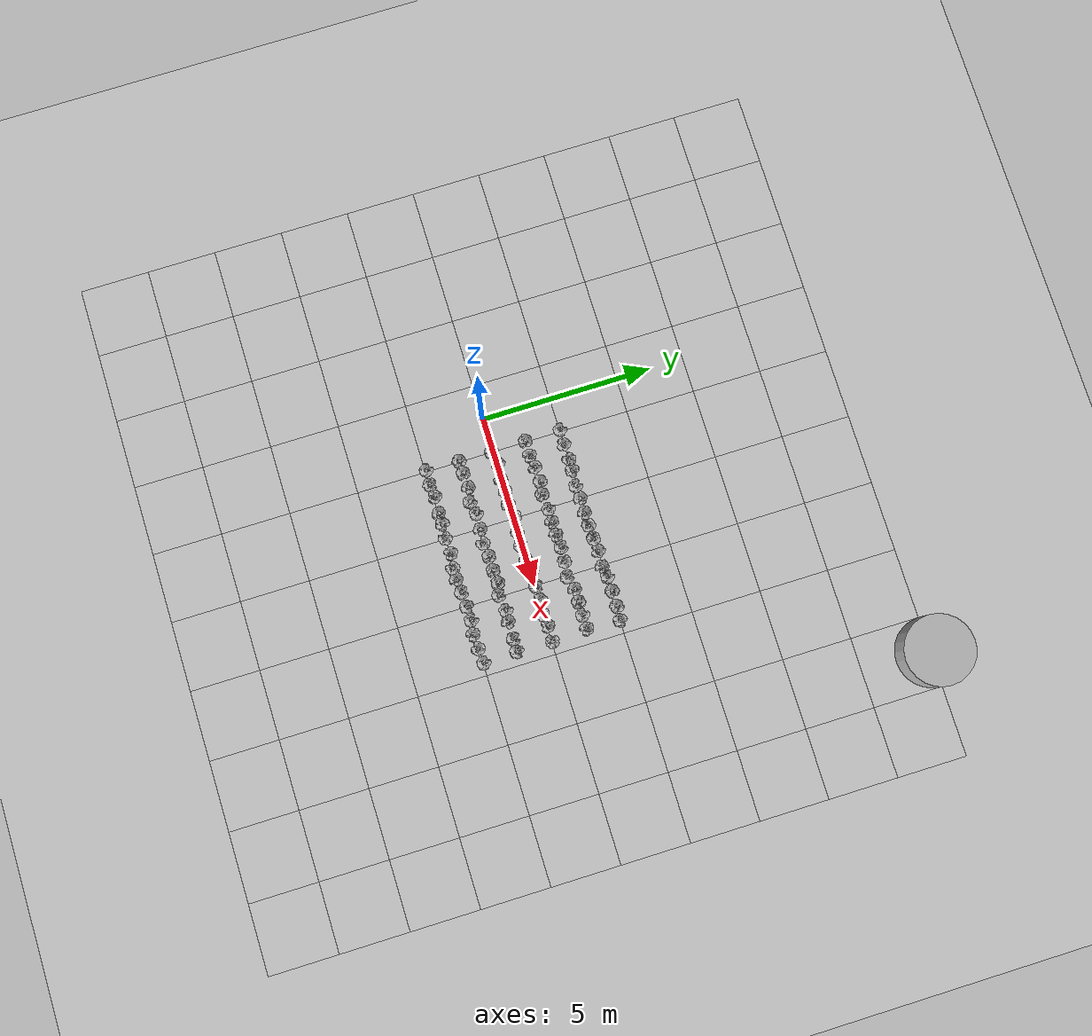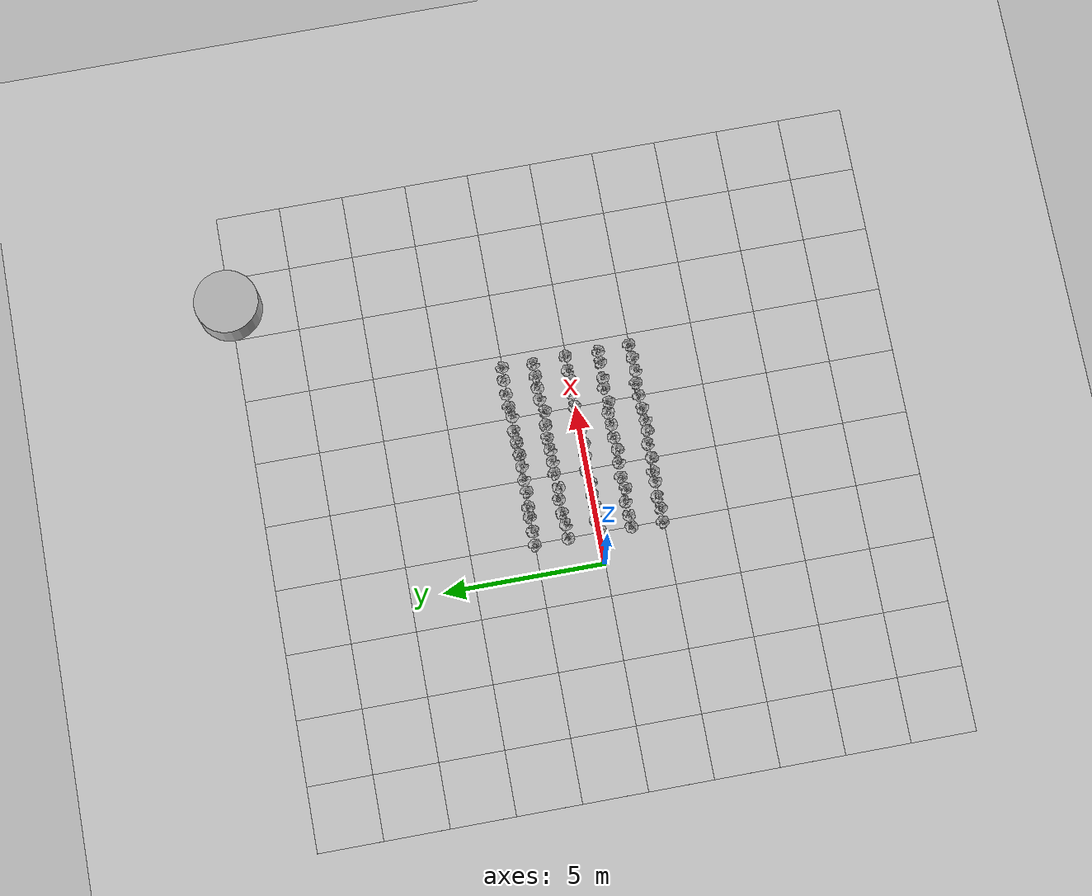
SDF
<?xml version="1.0" encoding="UTF-8"?>
<sdf version="1.9">
  <world name="default">
    <physics type="ode">
      <max_step_size>0.004</max_step_size>
      <real_time_factor>1.0</real_time_factor>
      <real_time_update_rate>250</real_time_update_rate>
    </physics>
    <gravity>0 0 -9.8</gravity>
    <magnetic_field>6e-06 2.3e-05 -4.2e-05</magnetic_field>
    <atmosphere type="adiabatic"/>
    <scene>
      <grid>false</grid>
      <ambient>0.4 0.4 0.4 1</ambient>
      <background>0.7 0.7 0.7 1</background>
      <shadows>true</shadows>
    </scene>
    <model name="ground_plane">
      <static>true</static>
      <link name="link">
        <collision name="collision">
          <geometry>
            <plane>
              <normal>0 0 1</normal>
              <size>1 1</size>
            </plane>
          </geometry>
          <surface>
            <friction>
              <ode/>
            </friction>
            <bounce/>
            <contact/>
          </surface>
        </collision>
        <visual name="visual">
          <geometry>
            <plane>
              <normal>0 0 1</normal>
              <size>500 500</size>
            </plane>
          </geometry>
          <material>
            <ambient>0.8 0.8 0.8 1</ambient>
            <diffuse>0.8 0.8 0.8 1</diffuse>
            <specular>0.8 0.8 0.8 1</specular>
             <pbr>
              <metal>
                <albedo_map>models://ground_plane_textures/brown_mud_dry_diff_4k.jpg</albedo_map>
                <roughness>0.9</roughness>
                <metalness>0.0</metalness>
              </metal>
            </pbr>
          </material>
        </visual>
        <pose>0 0 0 0 -0 0</pose>
        <inertial>
          <pose>0 0 0 0 -0 0</pose>
          <mass>1</mass>
          <inertia>
            <ixx>1</ixx>
            <ixy>0</ixy>
            <ixz>0</ixz>
            <iyy>1</iyy>
            <iyz>0</iyz>
            <izz>1</izz>
          </inertia>
        </inertial>
        <enable_wind>false</enable_wind>
      </link>
      <pose>0 0 0 0 -0 0</pose>
      <self_collide>false</self_collide>
    </model>
    <light name="sunUTC" type="directional">
      <pose>0 0 500 0 -0 0</pose>
      <cast_shadows>true</cast_shadows>
      <intensity>1</intensity>
      <direction>0.001 0.625 -0.78</direction>
      <diffuse>0.904 0.904 0.904 1</diffuse>
      <specular>0.271 0.271 0.271 1</specular>
      <attenuation>
        <range>2000</range>
        <linear>0</linear>
        <constant>1</constant>
        <quadratic>0</quadratic>
      </attenuation>
      <spot>
        <inner_angle>0</inner_angle>
        <outer_angle>0</outer_angle>
        <falloff>0</falloff>
      </spot>
    </light>
    <spherical_coordinates>
      <surface_model>EARTH_WGS84</surface_model>
      <world_frame_orientation>ENU</world_frame_orientation>
      <latitude_deg>42.292467</latitude_deg>
      <longitude_deg>-71.262652</longitude_deg>
      <elevation>0</elevation>
    </spherical_coordinates>

<model name="swarm">

<link name="ref">
      <inertial>
        <pose>10 10 0 0 0 0</pose>
        <mass>100</mass>
        <inertia>
          <ixx>33.33</ixx>
          <ixy>0</ixy>
          <ixz>0</ixz>
          <iyy>33.33</iyy>
          <iyz>0</iyz>
          <izz>50</izz>
        </inertia>
      </inertial>
      <collision name="ref_collision">
        <pose>10 10 0.5 0 0 0</pose>
        <geometry>
          <cylinder>
            <length>1</length>
            <radius>1</radius>
          </cylinder>
        </geometry>
      </collision>
      <visual name="ref_visual">
        <pose>10 10 0.5 0 0 0</pose>
        <geometry>
          <cylinder>
            <length>1</length>
            <radius>1</radius>
          </cylinder>
        </geometry>
      </visual>
    </link>

      <include>
        <uri>lettuce_bib</uri>
        <name>lettuce_bib_1</name>
        <pose>0.955 -1.956 0 0 0 2.119</pose>
      </include>
      <include>
        <uri>lettuce_bib</uri>
        <name>lettuce_bib_2</name>
        <pose>1.391 -1.979 0 0 0 1.280</pose>
      </include>
      <include>
        <uri>lettuce_bib</uri>
        <name>lettuce_bib_3</name>
        <pose>1.759 -1.951 0 0 0 -1.864</pose>
      </include>
      <include>
        <uri>lettuce_bib</uri>
        <name>lettuce_bib_4</name>
        <pose>2.248 -1.977 0 0 0 -0.654</pose>
      </include>
      <include>
        <uri>lettuce_bib</uri>
        <name>lettuce_bib_5</name>
        <pose>2.571 -1.967 0 0 0 0.595</pose>
      </include>
      <include>
        <uri>lettuce_bib</uri>
        <name>lettuce_bib_6</name>
        <pose>2.980 -2.010 0 0 0 -2.887</pose>
      </include>
      <include>
        <uri>lettuce_bib</uri>
        <name>lettuce_bib_7</name>
        <pose>3.436 -1.980 0 0 0 -1.515</pose>
      </include>
      <include>
        <uri>lettuce_bib</uri>
        <name>lettuce_bib_8</name>
        <pose>3.846 -2.041 0 0 0 -2.746</pose>
      </include>
      <include>
        <uri>lettuce_bib</uri>
        <name>lettuce_bib_9</name>
        <pose>4.186 -2.046 0 0 0 -0.740</pose>
      </include>
      <include>
        <uri>lettuce_bib</uri>
        <name>lettuce_bib_10</name>
        <pose>4.578 -2.004 0 0 0 1.537</pose>
      </include>
      <include>
        <uri>lettuce_bib</uri>
        <name>lettuce_bib_11</name>
        <pose>5.006 -1.979 0 0 0 0.884</pose>
      </include>
      <include>
        <uri>lettuce_bib</uri>
        <name>lettuce_bib_12</name>
        <pose>5.397 -1.964 0 0 0 1.962</pose>
      </include>
      <include>
        <uri>lettuce_bib</uri>
        <name>lettuce_bib_13</name>
        <pose>5.800 -2.043 0 0 0 -1.235</pose>
      </include>
      <include>
        <uri>lettuce_bib</uri>
        <name>lettuce_bib_14</name>
        <pose>6.211 -2.022 0 0 0 -2.442</pose>
      </include>
      <include>
        <uri>lettuce_bib</uri>
        <name>lettuce_bib_15</name>
        <pose>6.637 -1.975 0 0 0 2.100</pose>
      </include>
      <include>
        <uri>lettuce_bib</uri>
        <name>lettuce_bib_16</name>
        <pose>0.983 -0.998 0 0 0 0.118</pose>
      </include>
      <include>
        <uri>lettuce_bib</uri>
        <name>lettuce_bib_17</name>
        <pose>1.351 -0.988 0 0 0 -0.099</pose>
      </include>
      <include>
        <uri>lettuce_bib</uri>
        <name>lettuce_bib_18</name>
        <pose>1.785 -0.967 0 0 0 -0.917</pose>
      </include>
      <include>
        <uri>lettuce_bib</uri>
        <name>lettuce_bib_19</name>
        <pose>2.189 -1.032 0 0 0 1.815</pose>
      </include>
      <include>
        <uri>lettuce_bib</uri>
        <name>lettuce_bib_20</name>
        <pose>2.562 -0.957 0 0 0 2.045</pose>
      </include>
      <include>
        <uri>lettuce_bib</uri>
        <name>lettuce_bib_21</name>
        <pose>3.025 -0.990 0 0 0 -0.830</pose>
      </include>
      <include>
        <uri>lettuce_bib</uri>
        <name>lettuce_bib_22</name>
        <pose>3.425 -1.026 0 0 0 -2.745</pose>
      </include>
      <include>
        <uri>lettuce_bib</uri>
        <name>lettuce_bib_23</name>
        <pose>3.832 -0.977 0 0 0 -0.189</pose>
      </include>
      <include>
        <uri>lettuce_bib</uri>
        <name>lettuce_bib_24</name>
        <pose>4.245 -0.981 0 0 0 -0.171</pose>
      </include>
      <include>
        <uri>lettuce_bib</uri>
        <name>lettuce_bib_25</name>
        <pose>4.623 -0.957 0 0 0 -0.419</pose>
      </include>
      <include>
        <uri>lettuce_bib</uri>
        <name>lettuce_bib_26</name>
        <pose>4.960 -1.026 0 0 0 1.534</pose>
      </include>
      <include>
        <uri>lettuce_bib</uri>
        <name>lettuce_bib_27</name>
        <pose>5.423 -0.961 0 0 0 2.166</pose>
      </include>
      <include>
        <uri>lettuce_bib</uri>
        <name>lettuce_bib_28</name>
        <pose>5.750 -1.002 0 0 0 -0.741</pose>
      </include>
      <include>
        <uri>lettuce_bib</uri>
        <name>lettuce_bib_29</name>
        <pose>6.244 -0.998 0 0 0 1.466</pose>
      </include>
      <include>
        <uri>lettuce_bib</uri>
        <name>lettuce_bib_30</name>
        <pose>6.619 -1.009 0 0 0 0.898</pose>
      </include>
      <include>
        <uri>lettuce_bib</uri>
        <name>lettuce_bib_31</name>
        <pose>1.012 -0.039 0 0 0 0.933</pose>
      </include>
      <include>
        <uri>lettuce_bib</uri>
        <name>lettuce_bib_32</name>
        <pose>1.374 0.034 0 0 0 -1.955</pose>
      </include>
      <include>
        <uri>lettuce_bib</uri>
        <name>lettuce_bib_33</name>
        <pose>1.824 -0.021 0 0 0 -2.300</pose>
      </include>
      <include>
        <uri>lettuce_bib</uri>
        <name>lettuce_bib_34</name>
        <pose>2.196 -0.001 0 0 0 2.654</pose>
      </include>
      <include>
        <uri>lettuce_bib</uri>
        <name>lettuce_bib_35</name>
        <pose>2.577 -0.027 0 0 0 0.711</pose>
      </include>
      <include>
        <uri>lettuce_bib</uri>
        <name>lettuce_bib_36</name>
        <pose>2.962 0.049 0 0 0 2.907</pose>
      </include>
      <include>
        <uri>lettuce_bib</uri>
        <name>lettuce_bib_37</name>
        <pose>3.391 -0.001 0 0 0 1.690</pose>
      </include>
      <include>
        <uri>lettuce_bib</uri>
        <name>lettuce_bib_38</name>
        <pose>3.790 -0.041 0 0 0 2.475</pose>
      </include>
      <include>
        <uri>lettuce_bib</uri>
        <name>lettuce_bib_39</name>
        <pose>4.244 -0.009 0 0 0 -0.041</pose>
      </include>
      <include>
        <uri>lettuce_bib</uri>
        <name>lettuce_bib_40</name>
        <pose>4.591 0.043 0 0 0 1.789</pose>
      </include>
      <include>
        <uri>lettuce_bib</uri>
        <name>lettuce_bib_41</name>
        <pose>5.024 0.039 0 0 0 1.230</pose>
      </include>
      <include>
        <uri>lettuce_bib</uri>
        <name>lettuce_bib_42</name>
        <pose>5.436 0.046 0 0 0 0.347</pose>
      </include>
      <include>
        <uri>lettuce_bib</uri>
        <name>lettuce_bib_43</name>
        <pose>5.829 -0.019 0 0 0 2.762</pose>
      </include>
      <include>
        <uri>lettuce_bib</uri>
        <name>lettuce_bib_44</name>
        <pose>6.178 0.022 0 0 0 -1.627</pose>
      </include>
      <include>
        <uri>lettuce_bib</uri>
        <name>lettuce_bib_45</name>
        <pose>6.632 0.026 0 0 0 2.745</pose>
      </include>
      <include>
        <uri>lettuce_bib</uri>
        <name>lettuce_bib_46</name>
        <pose>0.983 0.968 0 0 0 -0.177</pose>
      </include>
      <include>
        <uri>lettuce_bib</uri>
        <name>lettuce_bib_47</name>
        <pose>1.418 0.956 0 0 0 -1.452</pose>
      </include>
      <include>
        <uri>lettuce_bib</uri>
        <name>lettuce_bib_48</name>
        <pose>1.773 1.006 0 0 0 -2.163</pose>
      </include>
      <include>
        <uri>lettuce_bib</uri>
        <name>lettuce_bib_49</name>
        <pose>2.223 1.031 0 0 0 0.104</pose>
      </include>
      <include>
        <uri>lettuce_bib</uri>
        <name>lettuce_bib_50</name>
        <pose>2.592 0.972 0 0 0 0.043</pose>
      </include>
      <include>
        <uri>lettuce_bib</uri>
        <name>lettuce_bib_51</name>
        <pose>3.039 1.029 0 0 0 2.261</pose>
      </include>
      <include>
        <uri>lettuce_bib</uri>
        <name>lettuce_bib_52</name>
        <pose>3.419 1.002 0 0 0 -1.135</pose>
      </include>
      <include>
        <uri>lettuce_bib</uri>
        <name>lettuce_bib_53</name>
        <pose>3.804 1.001 0 0 0 -1.355</pose>
      </include>
      <include>
        <uri>lettuce_bib</uri>
        <name>lettuce_bib_54</name>
        <pose>4.178 1.045 0 0 0 1.638</pose>
      </include>
      <include>
        <uri>lettuce_bib</uri>
        <name>lettuce_bib_55</name>
        <pose>4.591 1.013 0 0 0 3.028</pose>
      </include>
      <include>
        <uri>lettuce_bib</uri>
        <name>lettuce_bib_56</name>
        <pose>5.029 0.957 0 0 0 1.559</pose>
      </include>
      <include>
        <uri>lettuce_bib</uri>
        <name>lettuce_bib_57</name>
        <pose>5.426 1.048 0 0 0 -0.856</pose>
      </include>
      <include>
        <uri>lettuce_bib</uri>
        <name>lettuce_bib_58</name>
        <pose>5.797 1.047 0 0 0 0.049</pose>
      </include>
      <include>
        <uri>lettuce_bib</uri>
        <name>lettuce_bib_59</name>
        <pose>6.170 1.048 0 0 0 2.201</pose>
      </include>
      <include>
        <uri>lettuce_bib</uri>
        <name>lettuce_bib_60</name>
        <pose>6.579 1.038 0 0 0 -1.364</pose>
      </include>
      <include>
        <uri>lettuce_bib</uri>
        <name>lettuce_bib_61</name>
        <pose>0.956 2.016 0 0 0 2.075</pose>
      </include>
      <include>
        <uri>lettuce_bib</uri>
        <name>lettuce_bib_62</name>
        <pose>1.387 1.984 0 0 0 -1.959</pose>
      </include>
      <include>
        <uri>lettuce_bib</uri>
        <name>lettuce_bib_63</name>
        <pose>1.840 2.006 0 0 0 -2.767</pose>
      </include>
      <include>
        <uri>lettuce_bib</uri>
        <name>lettuce_bib_64</name>
        <pose>2.176 2.001 0 0 0 0.741</pose>
      </include>
      <include>
        <uri>lettuce_bib</uri>
        <name>lettuce_bib_65</name>
        <pose>2.631 1.960 0 0 0 1.964</pose>
      </include>
      <include>
        <uri>lettuce_bib</uri>
        <name>lettuce_bib_66</name>
        <pose>3.015 1.969 0 0 0 -0.675</pose>
      </include>
      <include>
        <uri>lettuce_bib</uri>
        <name>lettuce_bib_67</name>
        <pose>3.446 1.954 0 0 0 -0.992</pose>
      </include>
      <include>
        <uri>lettuce_bib</uri>
        <name>lettuce_bib_68</name>
        <pose>3.816 1.969 0 0 0 -3.037</pose>
      </include>
      <include>
        <uri>lettuce_bib</uri>
        <name>lettuce_bib_69</name>
        <pose>4.219 1.986 0 0 0 3.075</pose>
      </include>
      <include>
        <uri>lettuce_bib</uri>
        <name>lettuce_bib_70</name>
        <pose>4.580 2.000 0 0 0 -1.989</pose>
      </include>
      <include>
        <uri>lettuce_bib</uri>
        <name>lettuce_bib_71</name>
        <pose>5.043 1.969 0 0 0 -0.959</pose>
      </include>
      <include>
        <uri>lettuce_bib</uri>
        <name>lettuce_bib_72</name>
        <pose>5.356 2.038 0 0 0 1.985</pose>
      </include>
      <include>
        <uri>lettuce_bib</uri>
        <name>lettuce_bib_73</name>
        <pose>5.784 2.040 0 0 0 0.147</pose>
      </include>
      <include>
        <uri>lettuce_bib</uri>
        <name>lettuce_bib_74</name>
        <pose>6.228 2.035 0 0 0 -0.027</pose>
      </include>
      <include>
        <uri>lettuce_bib</uri>
        <name>lettuce_bib_75</name>
        <pose>6.636 2.009 0 0 0 0.875</pose>
      </include>

    </model>

    <model name="soil_grid">
      <static>true</static>
      <link name="link">
        <visual name="soil_patch_1">
          <pose>-6.000 -9.000 0.005 0 0 0</pose>
          <geometry>
            <plane>
              <normal>0 0 1</normal>
              <size>2.000 2.000</size>
            </plane>
          </geometry>
          <material>
            <ambient>0.8 0.8 0.8 1</ambient>
            <diffuse>0.8 0.8 0.8 1</diffuse>
            <specular>0.1 0.1 0.1 1</specular>
            <pbr>
              <metal>
                <albedo_map>models://ground_plane_textures/brown_mud_dry_diff_4k.jpg</albedo_map>
                <roughness>0.9</roughness>
                <metalness>0.0</metalness>
              </metal>
            </pbr>
          </material>
        </visual>
        <visual name="soil_patch_2">
          <pose>-6.000 -7.000 0.005 0 0 0</pose>
          <geometry>
            <plane>
              <normal>0 0 1</normal>
              <size>2.000 2.000</size>
            </plane>
          </geometry>
          <material>
            <ambient>0.8 0.8 0.8 1</ambient>
            <diffuse>0.8 0.8 0.8 1</diffuse>
            <specular>0.1 0.1 0.1 1</specular>
            <pbr>
              <metal>
                <albedo_map>models://ground_plane_textures/brown_mud_dry_diff_4k.jpg</albedo_map>
                <roughness>0.9</roughness>
                <metalness>0.0</metalness>
              </metal>
            </pbr>
          </material>
        </visual>
        <visual name="soil_patch_3">
          <pose>-6.000 -5.000 0.005 0 0 0</pose>
          <geometry>
            <plane>
              <normal>0 0 1</normal>
              <size>2.000 2.000</size>
            </plane>
          </geometry>
          <material>
            <ambient>0.8 0.8 0.8 1</ambient>
            <diffuse>0.8 0.8 0.8 1</diffuse>
            <specular>0.1 0.1 0.1 1</specular>
            <pbr>
              <metal>
                <albedo_map>models://ground_plane_textures/brown_mud_dry_diff_4k.jpg</albedo_map>
                <roughness>0.9</roughness>
                <metalness>0.0</metalness>
              </metal>
            </pbr>
          </material>
        </visual>
        <visual name="soil_patch_4">
          <pose>-6.000 -3.000 0.005 0 0 0</pose>
          <geometry>
            <plane>
              <normal>0 0 1</normal>
              <size>2.000 2.000</size>
            </plane>
          </geometry>
          <material>
            <ambient>0.8 0.8 0.8 1</ambient>
            <diffuse>0.8 0.8 0.8 1</diffuse>
            <specular>0.1 0.1 0.1 1</specular>
            <pbr>
              <metal>
                <albedo_map>models://ground_plane_textures/brown_mud_dry_diff_4k.jpg</albedo_map>
                <roughness>0.9</roughness>
                <metalness>0.0</metalness>
              </metal>
            </pbr>
          </material>
        </visual>
        <visual name="soil_patch_5">
          <pose>-6.000 -1.000 0.005 0 0 0</pose>
          <geometry>
            <plane>
              <normal>0 0 1</normal>
              <size>2.000 2.000</size>
            </plane>
          </geometry>
          <material>
            <ambient>0.8 0.8 0.8 1</ambient>
            <diffuse>0.8 0.8 0.8 1</diffuse>
            <specular>0.1 0.1 0.1 1</specular>
            <pbr>
              <metal>
                <albedo_map>models://ground_plane_textures/brown_mud_dry_diff_4k.jpg</albedo_map>
                <roughness>0.9</roughness>
                <metalness>0.0</metalness>
              </metal>
            </pbr>
          </material>
        </visual>
        <visual name="soil_patch_6">
          <pose>-6.000 1.000 0.005 0 0 0</pose>
          <geometry>
            <plane>
              <normal>0 0 1</normal>
              <size>2.000 2.000</size>
            </plane>
          </geometry>
          <material>
            <ambient>0.8 0.8 0.8 1</ambient>
            <diffuse>0.8 0.8 0.8 1</diffuse>
            <specular>0.1 0.1 0.1 1</specular>
            <pbr>
              <metal>
                <albedo_map>models://ground_plane_textures/brown_mud_dry_diff_4k.jpg</albedo_map>
                <roughness>0.9</roughness>
                <metalness>0.0</metalness>
              </metal>
            </pbr>
          </material>
        </visual>
        <visual name="soil_patch_7">
          <pose>-6.000 3.000 0.005 0 0 0</pose>
          <geometry>
            <plane>
              <normal>0 0 1</normal>
              <size>2.000 2.000</size>
            </plane>
          </geometry>
          <material>
            <ambient>0.8 0.8 0.8 1</ambient>
            <diffuse>0.8 0.8 0.8 1</diffuse>
            <specular>0.1 0.1 0.1 1</specular>
            <pbr>
              <metal>
                <albedo_map>models://ground_plane_textures/brown_mud_dry_diff_4k.jpg</albedo_map>
                <roughness>0.9</roughness>
                <metalness>0.0</metalness>
              </metal>
            </pbr>
          </material>
        </visual>
        <visual name="soil_patch_8">
          <pose>-6.000 5.000 0.005 0 0 0</pose>
          <geometry>
            <plane>
              <normal>0 0 1</normal>
              <size>2.000 2.000</size>
            </plane>
          </geometry>
          <material>
            <ambient>0.8 0.8 0.8 1</ambient>
            <diffuse>0.8 0.8 0.8 1</diffuse>
            <specular>0.1 0.1 0.1 1</specular>
            <pbr>
              <metal>
                <albedo_map>models://ground_plane_textures/brown_mud_dry_diff_4k.jpg</albedo_map>
                <roughness>0.9</roughness>
                <metalness>0.0</metalness>
              </metal>
            </pbr>
          </material>
        </visual>
        <visual name="soil_patch_9">
          <pose>-6.000 7.000 0.005 0 0 0</pose>
          <geometry>
            <plane>
              <normal>0 0 1</normal>
              <size>2.000 2.000</size>
            </plane>
          </geometry>
          <material>
            <ambient>0.8 0.8 0.8 1</ambient>
            <diffuse>0.8 0.8 0.8 1</diffuse>
            <specular>0.1 0.1 0.1 1</specular>
            <pbr>
              <metal>
                <albedo_map>models://ground_plane_textures/brown_mud_dry_diff_4k.jpg</albedo_map>
                <roughness>0.9</roughness>
                <metalness>0.0</metalness>
              </metal>
            </pbr>
          </material>
        </visual>
        <visual name="soil_patch_10">
          <pose>-6.000 9.000 0.005 0 0 0</pose>
          <geometry>
            <plane>
              <normal>0 0 1</normal>
              <size>2.000 2.000</size>
            </plane>
          </geometry>
          <material>
            <ambient>0.8 0.8 0.8 1</ambient>
            <diffuse>0.8 0.8 0.8 1</diffuse>
            <specular>0.1 0.1 0.1 1</specular>
            <pbr>
              <metal>
                <albedo_map>models://ground_plane_textures/brown_mud_dry_diff_4k.jpg</albedo_map>
                <roughness>0.9</roughness>
                <metalness>0.0</metalness>
              </metal>
            </pbr>
          </material>
        </visual>
        <visual name="soil_patch_11">
          <pose>-4.000 -9.000 0.005 0 0 0</pose>
          <geometry>
            <plane>
              <normal>0 0 1</normal>
              <size>2.000 2.000</size>
            </plane>
          </geometry>
          <material>
            <ambient>0.8 0.8 0.8 1</ambient>
            <diffuse>0.8 0.8 0.8 1</diffuse>
            <specular>0.1 0.1 0.1 1</specular>
            <pbr>
              <metal>
                <albedo_map>models://ground_plane_textures/brown_mud_dry_diff_4k.jpg</albedo_map>
                <roughness>0.9</roughness>
                <metalness>0.0</metalness>
              </metal>
            </pbr>
          </material>
        </visual>
        <visual name="soil_patch_12">
          <pose>-4.000 -7.000 0.005 0 0 0</pose>
          <geometry>
            <plane>
              <normal>0 0 1</normal>
              <size>2.000 2.000</size>
            </plane>
          </geometry>
          <material>
            <ambient>0.8 0.8 0.8 1</ambient>
            <diffuse>0.8 0.8 0.8 1</diffuse>
            <specular>0.1 0.1 0.1 1</specular>
            <pbr>
              <metal>
                <albedo_map>models://ground_plane_textures/brown_mud_dry_diff_4k.jpg</albedo_map>
                <roughness>0.9</roughness>
                <metalness>0.0</metalness>
              </metal>
            </pbr>
          </material>
        </visual>
        <visual name="soil_patch_13">
          <pose>-4.000 -5.000 0.005 0 0 0</pose>
          <geometry>
            <plane>
              <normal>0 0 1</normal>
              <size>2.000 2.000</size>
            </plane>
          </geometry>
          <material>
            <ambient>0.8 0.8 0.8 1</ambient>
            <diffuse>0.8 0.8 0.8 1</diffuse>
            <specular>0.1 0.1 0.1 1</specular>
            <pbr>
              <metal>
                <albedo_map>models://ground_plane_textures/brown_mud_dry_diff_4k.jpg</albedo_map>
                <roughness>0.9</roughness>
                <metalness>0.0</metalness>
              </metal>
            </pbr>
          </material>
        </visual>
        <visual name="soil_patch_14">
          <pose>-4.000 -3.000 0.005 0 0 0</pose>
          <geometry>
            <plane>
              <normal>0 0 1</normal>
              <size>2.000 2.000</size>
            </plane>
          </geometry>
          <material>
            <ambient>0.8 0.8 0.8 1</ambient>
            <diffuse>0.8 0.8 0.8 1</diffuse>
            <specular>0.1 0.1 0.1 1</specular>
            <pbr>
              <metal>
                <albedo_map>models://ground_plane_textures/brown_mud_dry_diff_4k.jpg</albedo_map>
                <roughness>0.9</roughness>
                <metalness>0.0</metalness>
              </metal>
            </pbr>
          </material>
        </visual>
        <visual name="soil_patch_15">
          <pose>-4.000 -1.000 0.005 0 0 0</pose>
          <geometry>
            <plane>
              <normal>0 0 1</normal>
              <size>2.000 2.000</size>
            </plane>
          </geometry>
          <material>
            <ambient>0.8 0.8 0.8 1</ambient>
            <diffuse>0.8 0.8 0.8 1</diffuse>
            <specular>0.1 0.1 0.1 1</specular>
            <pbr>
              <metal>
                <albedo_map>models://ground_plane_textures/brown_mud_dry_diff_4k.jpg</albedo_map>
                <roughness>0.9</roughness>
                <metalness>0.0</metalness>
              </metal>
            </pbr>
          </material>
        </visual>
        <visual name="soil_patch_16">
          <pose>-4.000 1.000 0.005 0 0 0</pose>
          <geometry>
            <plane>
              <normal>0 0 1</normal>
              <size>2.000 2.000</size>
            </plane>
          </geometry>
          <material>
            <ambient>0.8 0.8 0.8 1</ambient>
            <diffuse>0.8 0.8 0.8 1</diffuse>
            <specular>0.1 0.1 0.1 1</specular>
            <pbr>
              <metal>
                <albedo_map>models://ground_plane_textures/brown_mud_dry_diff_4k.jpg</albedo_map>
                <roughness>0.9</roughness>
                <metalness>0.0</metalness>
              </metal>
            </pbr>
          </material>
        </visual>
        <visual name="soil_patch_17">
          <pose>-4.000 3.000 0.005 0 0 0</pose>
          <geometry>
            <plane>
              <normal>0 0 1</normal>
              <size>2.000 2.000</size>
            </plane>
          </geometry>
          <material>
            <ambient>0.8 0.8 0.8 1</ambient>
            <diffuse>0.8 0.8 0.8 1</diffuse>
            <specular>0.1 0.1 0.1 1</specular>
            <pbr>
              <metal>
                <albedo_map>models://ground_plane_textures/brown_mud_dry_diff_4k.jpg</albedo_map>
                <roughness>0.9</roughness>
                <metalness>0.0</metalness>
              </metal>
            </pbr>
          </material>
        </visual>
        <visual name="soil_patch_18">
          <pose>-4.000 5.000 0.005 0 0 0</pose>
          <geometry>
            <plane>
              <normal>0 0 1</normal>
              <size>2.000 2.000</size>
            </plane>
          </geometry>
          <material>
            <ambient>0.8 0.8 0.8 1</ambient>
            <diffuse>0.8 0.8 0.8 1</diffuse>
            <specular>0.1 0.1 0.1 1</specular>
            <pbr>
              <metal>
                <albedo_map>models://ground_plane_textures/brown_mud_dry_diff_4k.jpg</albedo_map>
                <roughness>0.9</roughness>
                <metalness>0.0</metalness>
              </metal>
            </pbr>
          </material>
        </visual>
        <visual name="soil_patch_19">
          <pose>-4.000 7.000 0.005 0 0 0</pose>
          <geometry>
            <plane>
              <normal>0 0 1</normal>
              <size>2.000 2.000</size>
            </plane>
          </geometry>
          <material>
            <ambient>0.8 0.8 0.8 1</ambient>
            <diffuse>0.8 0.8 0.8 1</diffuse>
            <specular>0.1 0.1 0.1 1</specular>
            <pbr>
              <metal>
                <albedo_map>models://ground_plane_textures/brown_mud_dry_diff_4k.jpg</albedo_map>
                <roughness>0.9</roughness>
                <metalness>0.0</metalness>
              </metal>
            </pbr>
          </material>
        </visual>
        <visual name="soil_patch_20">
          <pose>-4.000 9.000 0.005 0 0 0</pose>
          <geometry>
            <plane>
              <normal>0 0 1</normal>
              <size>2.000 2.000</size>
            </plane>
          </geometry>
          <material>
            <ambient>0.8 0.8 0.8 1</ambient>
            <diffuse>0.8 0.8 0.8 1</diffuse>
            <specular>0.1 0.1 0.1 1</specular>
            <pbr>
              <metal>
                <albedo_map>models://ground_plane_textures/brown_mud_dry_diff_4k.jpg</albedo_map>
                <roughness>0.9</roughness>
                <metalness>0.0</metalness>
              </metal>
            </pbr>
          </material>
        </visual>
        <visual name="soil_patch_21">
          <pose>-2.000 -9.000 0.005 0 0 0</pose>
          <geometry>
            <plane>
              <normal>0 0 1</normal>
              <size>2.000 2.000</size>
            </plane>
          </geometry>
          <material>
            <ambient>0.8 0.8 0.8 1</ambient>
            <diffuse>0.8 0.8 0.8 1</diffuse>
            <specular>0.1 0.1 0.1 1</specular>
            <pbr>
              <metal>
                <albedo_map>models://ground_plane_textures/brown_mud_dry_diff_4k.jpg</albedo_map>
                <roughness>0.9</roughness>
                <metalness>0.0</metalness>
              </metal>
            </pbr>
          </material>
        </visual>
        <visual name="soil_patch_22">
          <pose>-2.000 -7.000 0.005 0 0 0</pose>
          <geometry>
            <plane>
              <normal>0 0 1</normal>
              <size>2.000 2.000</size>
            </plane>
          </geometry>
          <material>
            <ambient>0.8 0.8 0.8 1</ambient>
            <diffuse>0.8 0.8 0.8 1</diffuse>
            <specular>0.1 0.1 0.1 1</specular>
            <pbr>
              <metal>
                <albedo_map>models://ground_plane_textures/brown_mud_dry_diff_4k.jpg</albedo_map>
                <roughness>0.9</roughness>
                <metalness>0.0</metalness>
              </metal>
            </pbr>
          </material>
        </visual>
        <visual name="soil_patch_23">
          <pose>-2.000 -5.000 0.005 0 0 0</pose>
          <geometry>
            <plane>
              <normal>0 0 1</normal>
              <size>2.000 2.000</size>
            </plane>
          </geometry>
          <material>
            <ambient>0.8 0.8 0.8 1</ambient>
            <diffuse>0.8 0.8 0.8 1</diffuse>
            <specular>0.1 0.1 0.1 1</specular>
            <pbr>
              <metal>
                <albedo_map>models://ground_plane_textures/brown_mud_dry_diff_4k.jpg</albedo_map>
                <roughness>0.9</roughness>
                <metalness>0.0</metalness>
              </metal>
            </pbr>
          </material>
        </visual>
        <visual name="soil_patch_24">
          <pose>-2.000 -3.000 0.005 0 0 0</pose>
          <geometry>
            <plane>
              <normal>0 0 1</normal>
              <size>2.000 2.000</size>
            </plane>
          </geometry>
          <material>
            <ambient>0.8 0.8 0.8 1</ambient>
            <diffuse>0.8 0.8 0.8 1</diffuse>
            <specular>0.1 0.1 0.1 1</specular>
            <pbr>
              <metal>
                <albedo_map>models://ground_plane_textures/brown_mud_dry_diff_4k.jpg</albedo_map>
                <roughness>0.9</roughness>
                <metalness>0.0</metalness>
              </metal>
            </pbr>
          </material>
        </visual>
        <visual name="soil_patch_25">
          <pose>-2.000 -1.000 0.005 0 0 0</pose>
          <geometry>
            <plane>
              <normal>0 0 1</normal>
              <size>2.000 2.000</size>
            </plane>
          </geometry>
          <material>
            <ambient>0.8 0.8 0.8 1</ambient>
            <diffuse>0.8 0.8 0.8 1</diffuse>
            <specular>0.1 0.1 0.1 1</specular>
            <pbr>
              <metal>
                <albedo_map>models://ground_plane_textures/brown_mud_dry_diff_4k.jpg</albedo_map>
                <roughness>0.9</roughness>
                <metalness>0.0</metalness>
              </metal>
            </pbr>
          </material>
        </visual>
        <visual name="soil_patch_26">
          <pose>-2.000 1.000 0.005 0 0 0</pose>
          <geometry>
            <plane>
              <normal>0 0 1</normal>
              <size>2.000 2.000</size>
            </plane>
          </geometry>
          <material>
            <ambient>0.8 0.8 0.8 1</ambient>
            <diffuse>0.8 0.8 0.8 1</diffuse>
            <specular>0.1 0.1 0.1 1</specular>
            <pbr>
              <metal>
                <albedo_map>models://ground_plane_textures/brown_mud_dry_diff_4k.jpg</albedo_map>
                <roughness>0.9</roughness>
                <metalness>0.0</metalness>
              </metal>
            </pbr>
          </material>
        </visual>
        <visual name="soil_patch_27">
          <pose>-2.000 3.000 0.005 0 0 0</pose>
          <geometry>
            <plane>
              <normal>0 0 1</normal>
              <size>2.000 2.000</size>
            </plane>
          </geometry>
          <material>
            <ambient>0.8 0.8 0.8 1</ambient>
            <diffuse>0.8 0.8 0.8 1</diffuse>
            <specular>0.1 0.1 0.1 1</specular>
            <pbr>
              <metal>
                <albedo_map>models://ground_plane_textures/brown_mud_dry_diff_4k.jpg</albedo_map>
                <roughness>0.9</roughness>
                <metalness>0.0</metalness>
              </metal>
            </pbr>
          </material>
        </visual>
        <visual name="soil_patch_28">
          <pose>-2.000 5.000 0.005 0 0 0</pose>
          <geometry>
            <plane>
              <normal>0 0 1</normal>
              <size>2.000 2.000</size>
            </plane>
          </geometry>
          <material>
            <ambient>0.8 0.8 0.8 1</ambient>
            <diffuse>0.8 0.8 0.8 1</diffuse>
            <specular>0.1 0.1 0.1 1</specular>
            <pbr>
              <metal>
                <albedo_map>models://ground_plane_textures/brown_mud_dry_diff_4k.jpg</albedo_map>
                <roughness>0.9</roughness>
                <metalness>0.0</metalness>
              </metal>
            </pbr>
          </material>
        </visual>
        <visual name="soil_patch_29">
          <pose>-2.000 7.000 0.005 0 0 0</pose>
          <geometry>
            <plane>
              <normal>0 0 1</normal>
              <size>2.000 2.000</size>
            </plane>
          </geometry>
          <material>
            <ambient>0.8 0.8 0.8 1</ambient>
            <diffuse>0.8 0.8 0.8 1</diffuse>
            <specular>0.1 0.1 0.1 1</specular>
            <pbr>
              <metal>
                <albedo_map>models://ground_plane_textures/brown_mud_dry_diff_4k.jpg</albedo_map>
                <roughness>0.9</roughness>
                <metalness>0.0</metalness>
              </metal>
            </pbr>
          </material>
        </visual>
        <visual name="soil_patch_30">
          <pose>-2.000 9.000 0.005 0 0 0</pose>
          <geometry>
            <plane>
              <normal>0 0 1</normal>
              <size>2.000 2.000</size>
            </plane>
          </geometry>
          <material>
            <ambient>0.8 0.8 0.8 1</ambient>
            <diffuse>0.8 0.8 0.8 1</diffuse>
            <specular>0.1 0.1 0.1 1</specular>
            <pbr>
              <metal>
                <albedo_map>models://ground_plane_textures/brown_mud_dry_diff_4k.jpg</albedo_map>
                <roughness>0.9</roughness>
                <metalness>0.0</metalness>
              </metal>
            </pbr>
          </material>
        </visual>
        <visual name="soil_patch_31">
          <pose>0.000 -9.000 0.005 0 0 0</pose>
          <geometry>
            <plane>
              <normal>0 0 1</normal>
              <size>2.000 2.000</size>
            </plane>
          </geometry>
          <material>
            <ambient>0.8 0.8 0.8 1</ambient>
            <diffuse>0.8 0.8 0.8 1</diffuse>
            <specular>0.1 0.1 0.1 1</specular>
            <pbr>
              <metal>
                <albedo_map>models://ground_plane_textures/brown_mud_dry_diff_4k.jpg</albedo_map>
                <roughness>0.9</roughness>
                <metalness>0.0</metalness>
              </metal>
            </pbr>
          </material>
        </visual>
        <visual name="soil_patch_32">
          <pose>0.000 -7.000 0.005 0 0 0</pose>
          <geometry>
            <plane>
              <normal>0 0 1</normal>
              <size>2.000 2.000</size>
            </plane>
          </geometry>
          <material>
            <ambient>0.8 0.8 0.8 1</ambient>
            <diffuse>0.8 0.8 0.8 1</diffuse>
            <specular>0.1 0.1 0.1 1</specular>
            <pbr>
              <metal>
                <albedo_map>models://ground_plane_textures/brown_mud_dry_diff_4k.jpg</albedo_map>
                <roughness>0.9</roughness>
                <metalness>0.0</metalness>
              </metal>
            </pbr>
          </material>
        </visual>
        <visual name="soil_patch_33">
          <pose>0.000 -5.000 0.005 0 0 0</pose>
          <geometry>
            <plane>
              <normal>0 0 1</normal>
              <size>2.000 2.000</size>
            </plane>
          </geometry>
          <material>
            <ambient>0.8 0.8 0.8 1</ambient>
            <diffuse>0.8 0.8 0.8 1</diffuse>
            <specular>0.1 0.1 0.1 1</specular>
            <pbr>
              <metal>
                <albedo_map>models://ground_plane_textures/brown_mud_dry_diff_4k.jpg</albedo_map>
                <roughness>0.9</roughness>
                <metalness>0.0</metalness>
              </metal>
            </pbr>
          </material>
        </visual>
        <visual name="soil_patch_34">
          <pose>0.000 -3.000 0.005 0 0 0</pose>
          <geometry>
            <plane>
              <normal>0 0 1</normal>
              <size>2.000 2.000</size>
            </plane>
          </geometry>
          <material>
            <ambient>0.8 0.8 0.8 1</ambient>
            <diffuse>0.8 0.8 0.8 1</diffuse>
            <specular>0.1 0.1 0.1 1</specular>
            <pbr>
              <metal>
                <albedo_map>models://ground_plane_textures/brown_mud_dry_diff_4k.jpg</albedo_map>
                <roughness>0.9</roughness>
                <metalness>0.0</metalness>
              </metal>
            </pbr>
          </material>
        </visual>
        <visual name="soil_patch_35">
          <pose>0.000 -1.000 0.005 0 0 0</pose>
          <geometry>
            <plane>
              <normal>0 0 1</normal>
              <size>2.000 2.000</size>
            </plane>
          </geometry>
          <material>
            <ambient>0.8 0.8 0.8 1</ambient>
            <diffuse>0.8 0.8 0.8 1</diffuse>
            <specular>0.1 0.1 0.1 1</specular>
            <pbr>
              <metal>
                <albedo_map>models://ground_plane_textures/brown_mud_dry_diff_4k.jpg</albedo_map>
                <roughness>0.9</roughness>
                <metalness>0.0</metalness>
              </metal>
            </pbr>
          </material>
        </visual>
        <visual name="soil_patch_36">
          <pose>0.000 1.000 0.005 0 0 0</pose>
          <geometry>
            <plane>
              <normal>0 0 1</normal>
              <size>2.000 2.000</size>
            </plane>
          </geometry>
          <material>
            <ambient>0.8 0.8 0.8 1</ambient>
            <diffuse>0.8 0.8 0.8 1</diffuse>
            <specular>0.1 0.1 0.1 1</specular>
            <pbr>
              <metal>
                <albedo_map>models://ground_plane_textures/brown_mud_dry_diff_4k.jpg</albedo_map>
                <roughness>0.9</roughness>
                <metalness>0.0</metalness>
              </metal>
            </pbr>
          </material>
        </visual>
        <visual name="soil_patch_37">
          <pose>0.000 3.000 0.005 0 0 0</pose>
          <geometry>
            <plane>
              <normal>0 0 1</normal>
              <size>2.000 2.000</size>
            </plane>
          </geometry>
          <material>
            <ambient>0.8 0.8 0.8 1</ambient>
            <diffuse>0.8 0.8 0.8 1</diffuse>
            <specular>0.1 0.1 0.1 1</specular>
            <pbr>
              <metal>
                <albedo_map>models://ground_plane_textures/brown_mud_dry_diff_4k.jpg</albedo_map>
                <roughness>0.9</roughness>
                <metalness>0.0</metalness>
              </metal>
            </pbr>
          </material>
        </visual>
        <visual name="soil_patch_38">
          <pose>0.000 5.000 0.005 0 0 0</pose>
          <geometry>
            <plane>
              <normal>0 0 1</normal>
              <size>2.000 2.000</size>
            </plane>
          </geometry>
          <material>
            <ambient>0.8 0.8 0.8 1</ambient>
            <diffuse>0.8 0.8 0.8 1</diffuse>
            <specular>0.1 0.1 0.1 1</specular>
            <pbr>
              <metal>
                <albedo_map>models://ground_plane_textures/brown_mud_dry_diff_4k.jpg</albedo_map>
                <roughness>0.9</roughness>
                <metalness>0.0</metalness>
              </metal>
            </pbr>
          </material>
        </visual>
        <visual name="soil_patch_39">
          <pose>0.000 7.000 0.005 0 0 0</pose>
          <geometry>
            <plane>
              <normal>0 0 1</normal>
              <size>2.000 2.000</size>
            </plane>
          </geometry>
          <material>
            <ambient>0.8 0.8 0.8 1</ambient>
            <diffuse>0.8 0.8 0.8 1</diffuse>
            <specular>0.1 0.1 0.1 1</specular>
            <pbr>
              <metal>
                <albedo_map>models://ground_plane_textures/brown_mud_dry_diff_4k.jpg</albedo_map>
                <roughness>0.9</roughness>
                <metalness>0.0</metalness>
              </metal>
            </pbr>
          </material>
        </visual>
        <visual name="soil_patch_40">
          <pose>0.000 9.000 0.005 0 0 0</pose>
          <geometry>
            <plane>
              <normal>0 0 1</normal>
              <size>2.000 2.000</size>
            </plane>
          </geometry>
          <material>
            <ambient>0.8 0.8 0.8 1</ambient>
            <diffuse>0.8 0.8 0.8 1</diffuse>
            <specular>0.1 0.1 0.1 1</specular>
            <pbr>
              <metal>
                <albedo_map>models://ground_plane_textures/brown_mud_dry_diff_4k.jpg</albedo_map>
                <roughness>0.9</roughness>
                <metalness>0.0</metalness>
              </metal>
            </pbr>
          </material>
        </visual>
        <visual name="soil_patch_41">
          <pose>2.000 -9.000 0.005 0 0 0</pose>
          <geometry>
            <plane>
              <normal>0 0 1</normal>
              <size>2.000 2.000</size>
            </plane>
          </geometry>
          <material>
            <ambient>0.8 0.8 0.8 1</ambient>
            <diffuse>0.8 0.8 0.8 1</diffuse>
            <specular>0.1 0.1 0.1 1</specular>
            <pbr>
              <metal>
                <albedo_map>models://ground_plane_textures/brown_mud_dry_diff_4k.jpg</albedo_map>
                <roughness>0.9</roughness>
                <metalness>0.0</metalness>
              </metal>
            </pbr>
          </material>
        </visual>
        <visual name="soil_patch_42">
          <pose>2.000 -7.000 0.005 0 0 0</pose>
          <geometry>
            <plane>
              <normal>0 0 1</normal>
              <size>2.000 2.000</size>
            </plane>
          </geometry>
          <material>
            <ambient>0.8 0.8 0.8 1</ambient>
            <diffuse>0.8 0.8 0.8 1</diffuse>
            <specular>0.1 0.1 0.1 1</specular>
            <pbr>
              <metal>
                <albedo_map>models://ground_plane_textures/brown_mud_dry_diff_4k.jpg</albedo_map>
                <roughness>0.9</roughness>
                <metalness>0.0</metalness>
              </metal>
            </pbr>
          </material>
        </visual>
        <visual name="soil_patch_43">
          <pose>2.000 -5.000 0.005 0 0 0</pose>
          <geometry>
            <plane>
              <normal>0 0 1</normal>
              <size>2.000 2.000</size>
            </plane>
          </geometry>
          <material>
            <ambient>0.8 0.8 0.8 1</ambient>
            <diffuse>0.8 0.8 0.8 1</diffuse>
            <specular>0.1 0.1 0.1 1</specular>
            <pbr>
              <metal>
                <albedo_map>models://ground_plane_textures/brown_mud_dry_diff_4k.jpg</albedo_map>
                <roughness>0.9</roughness>
                <metalness>0.0</metalness>
              </metal>
            </pbr>
          </material>
        </visual>
        <visual name="soil_patch_44">
          <pose>2.000 -3.000 0.005 0 0 0</pose>
          <geometry>
            <plane>
              <normal>0 0 1</normal>
              <size>2.000 2.000</size>
            </plane>
          </geometry>
          <material>
            <ambient>0.8 0.8 0.8 1</ambient>
            <diffuse>0.8 0.8 0.8 1</diffuse>
            <specular>0.1 0.1 0.1 1</specular>
            <pbr>
              <metal>
                <albedo_map>models://ground_plane_textures/brown_mud_dry_diff_4k.jpg</albedo_map>
                <roughness>0.9</roughness>
                <metalness>0.0</metalness>
              </metal>
            </pbr>
          </material>
        </visual>
        <visual name="soil_patch_45">
          <pose>2.000 -1.000 0.005 0 0 0</pose>
          <geometry>
            <plane>
              <normal>0 0 1</normal>
              <size>2.000 2.000</size>
            </plane>
          </geometry>
          <material>
            <ambient>0.8 0.8 0.8 1</ambient>
            <diffuse>0.8 0.8 0.8 1</diffuse>
            <specular>0.1 0.1 0.1 1</specular>
            <pbr>
              <metal>
                <albedo_map>models://ground_plane_textures/brown_mud_dry_diff_4k.jpg</albedo_map>
                <roughness>0.9</roughness>
                <metalness>0.0</metalness>
              </metal>
            </pbr>
          </material>
        </visual>
        <visual name="soil_patch_46">
          <pose>2.000 1.000 0.005 0 0 0</pose>
          <geometry>
            <plane>
              <normal>0 0 1</normal>
              <size>2.000 2.000</size>
            </plane>
          </geometry>
          <material>
            <ambient>0.8 0.8 0.8 1</ambient>
            <diffuse>0.8 0.8 0.8 1</diffuse>
            <specular>0.1 0.1 0.1 1</specular>
            <pbr>
              <metal>
                <albedo_map>models://ground_plane_textures/brown_mud_dry_diff_4k.jpg</albedo_map>
                <roughness>0.9</roughness>
                <metalness>0.0</metalness>
              </metal>
            </pbr>
          </material>
        </visual>
        <visual name="soil_patch_47">
          <pose>2.000 3.000 0.005 0 0 0</pose>
          <geometry>
            <plane>
              <normal>0 0 1</normal>
              <size>2.000 2.000</size>
            </plane>
          </geometry>
          <material>
            <ambient>0.8 0.8 0.8 1</ambient>
            <diffuse>0.8 0.8 0.8 1</diffuse>
            <specular>0.1 0.1 0.1 1</specular>
            <pbr>
              <metal>
                <albedo_map>models://ground_plane_textures/brown_mud_dry_diff_4k.jpg</albedo_map>
                <roughness>0.9</roughness>
                <metalness>0.0</metalness>
              </metal>
            </pbr>
          </material>
        </visual>
        <visual name="soil_patch_48">
          <pose>2.000 5.000 0.005 0 0 0</pose>
          <geometry>
            <plane>
              <normal>0 0 1</normal>
              <size>2.000 2.000</size>
            </plane>
          </geometry>
          <material>
            <ambient>0.8 0.8 0.8 1</ambient>
            <diffuse>0.8 0.8 0.8 1</diffuse>
            <specular>0.1 0.1 0.1 1</specular>
            <pbr>
              <metal>
                <albedo_map>models://ground_plane_textures/brown_mud_dry_diff_4k.jpg</albedo_map>
                <roughness>0.9</roughness>
                <metalness>0.0</metalness>
              </metal>
            </pbr>
          </material>
        </visual>
        <visual name="soil_patch_49">
          <pose>2.000 7.000 0.005 0 0 0</pose>
          <geometry>
            <plane>
              <normal>0 0 1</normal>
              <size>2.000 2.000</size>
            </plane>
          </geometry>
          <material>
            <ambient>0.8 0.8 0.8 1</ambient>
            <diffuse>0.8 0.8 0.8 1</diffuse>
            <specular>0.1 0.1 0.1 1</specular>
            <pbr>
              <metal>
                <albedo_map>models://ground_plane_textures/brown_mud_dry_diff_4k.jpg</albedo_map>
                <roughness>0.9</roughness>
                <metalness>0.0</metalness>
              </metal>
            </pbr>
          </material>
        </visual>
        <visual name="soil_patch_50">
          <pose>2.000 9.000 0.005 0 0 0</pose>
          <geometry>
            <plane>
              <normal>0 0 1</normal>
              <size>2.000 2.000</size>
            </plane>
          </geometry>
          <material>
            <ambient>0.8 0.8 0.8 1</ambient>
            <diffuse>0.8 0.8 0.8 1</diffuse>
            <specular>0.1 0.1 0.1 1</specular>
            <pbr>
              <metal>
                <albedo_map>models://ground_plane_textures/brown_mud_dry_diff_4k.jpg</albedo_map>
                <roughness>0.9</roughness>
                <metalness>0.0</metalness>
              </metal>
            </pbr>
          </material>
        </visual>
        <visual name="soil_patch_51">
          <pose>4.000 -9.000 0.005 0 0 0</pose>
          <geometry>
            <plane>
              <normal>0 0 1</normal>
              <size>2.000 2.000</size>
            </plane>
          </geometry>
          <material>
            <ambient>0.8 0.8 0.8 1</ambient>
            <diffuse>0.8 0.8 0.8 1</diffuse>
            <specular>0.1 0.1 0.1 1</specular>
            <pbr>
              <metal>
                <albedo_map>models://ground_plane_textures/brown_mud_dry_diff_4k.jpg</albedo_map>
                <roughness>0.9</roughness>
                <metalness>0.0</metalness>
              </metal>
            </pbr>
          </material>
        </visual>
        <visual name="soil_patch_52">
          <pose>4.000 -7.000 0.005 0 0 0</pose>
          <geometry>
            <plane>
              <normal>0 0 1</normal>
              <size>2.000 2.000</size>
            </plane>
          </geometry>
          <material>
            <ambient>0.8 0.8 0.8 1</ambient>
            <diffuse>0.8 0.8 0.8 1</diffuse>
            <specular>0.1 0.1 0.1 1</specular>
            <pbr>
              <metal>
                <albedo_map>models://ground_plane_textures/brown_mud_dry_diff_4k.jpg</albedo_map>
                <roughness>0.9</roughness>
                <metalness>0.0</metalness>
              </metal>
            </pbr>
          </material>
        </visual>
        <visual name="soil_patch_53">
          <pose>4.000 -5.000 0.005 0 0 0</pose>
          <geometry>
            <plane>
              <normal>0 0 1</normal>
              <size>2.000 2.000</size>
            </plane>
          </geometry>
          <material>
            <ambient>0.8 0.8 0.8 1</ambient>
            <diffuse>0.8 0.8 0.8 1</diffuse>
            <specular>0.1 0.1 0.1 1</specular>
            <pbr>
              <metal>
                <albedo_map>models://ground_plane_textures/brown_mud_dry_diff_4k.jpg</albedo_map>
                <roughness>0.9</roughness>
                <metalness>0.0</metalness>
              </metal>
            </pbr>
          </material>
        </visual>
        <visual name="soil_patch_54">
          <pose>4.000 -3.000 0.005 0 0 0</pose>
          <geometry>
            <plane>
              <normal>0 0 1</normal>
              <size>2.000 2.000</size>
            </plane>
          </geometry>
          <material>
            <ambient>0.8 0.8 0.8 1</ambient>
            <diffuse>0.8 0.8 0.8 1</diffuse>
            <specular>0.1 0.1 0.1 1</specular>
            <pbr>
              <metal>
                <albedo_map>models://ground_plane_textures/brown_mud_dry_diff_4k.jpg</albedo_map>
                <roughness>0.9</roughness>
                <metalness>0.0</metalness>
              </metal>
            </pbr>
          </material>
        </visual>
        <visual name="soil_patch_55">
          <pose>4.000 -1.000 0.005 0 0 0</pose>
          <geometry>
            <plane>
              <normal>0 0 1</normal>
              <size>2.000 2.000</size>
            </plane>
          </geometry>
          <material>
            <ambient>0.8 0.8 0.8 1</ambient>
            <diffuse>0.8 0.8 0.8 1</diffuse>
            <specular>0.1 0.1 0.1 1</specular>
            <pbr>
              <metal>
                <albedo_map>models://ground_plane_textures/brown_mud_dry_diff_4k.jpg</albedo_map>
                <roughness>0.9</roughness>
                <metalness>0.0</metalness>
              </metal>
            </pbr>
          </material>
        </visual>
        <visual name="soil_patch_56">
          <pose>4.000 1.000 0.005 0 0 0</pose>
          <geometry>
            <plane>
              <normal>0 0 1</normal>
              <size>2.000 2.000</size>
            </plane>
          </geometry>
          <material>
            <ambient>0.8 0.8 0.8 1</ambient>
            <diffuse>0.8 0.8 0.8 1</diffuse>
            <specular>0.1 0.1 0.1 1</specular>
            <pbr>
              <metal>
                <albedo_map>models://ground_plane_textures/brown_mud_dry_diff_4k.jpg</albedo_map>
                <roughness>0.9</roughness>
                <metalness>0.0</metalness>
              </metal>
            </pbr>
          </material>
        </visual>
        <visual name="soil_patch_57">
          <pose>4.000 3.000 0.005 0 0 0</pose>
          <geometry>
            <plane>
              <normal>0 0 1</normal>
              <size>2.000 2.000</size>
            </plane>
          </geometry>
          <material>
            <ambient>0.8 0.8 0.8 1</ambient>
            <diffuse>0.8 0.8 0.8 1</diffuse>
            <specular>0.1 0.1 0.1 1</specular>
            <pbr>
              <metal>
                <albedo_map>models://ground_plane_textures/brown_mud_dry_diff_4k.jpg</albedo_map>
                <roughness>0.9</roughness>
                <metalness>0.0</metalness>
              </metal>
            </pbr>
          </material>
        </visual>
        <visual name="soil_patch_58">
          <pose>4.000 5.000 0.005 0 0 0</pose>
          <geometry>
            <plane>
              <normal>0 0 1</normal>
              <size>2.000 2.000</size>
            </plane>
          </geometry>
          <material>
            <ambient>0.8 0.8 0.8 1</ambient>
            <diffuse>0.8 0.8 0.8 1</diffuse>
            <specular>0.1 0.1 0.1 1</specular>
            <pbr>
              <metal>
                <albedo_map>models://ground_plane_textures/brown_mud_dry_diff_4k.jpg</albedo_map>
                <roughness>0.9</roughness>
                <metalness>0.0</metalness>
              </metal>
            </pbr>
          </material>
        </visual>
        <visual name="soil_patch_59">
          <pose>4.000 7.000 0.005 0 0 0</pose>
          <geometry>
            <plane>
              <normal>0 0 1</normal>
              <size>2.000 2.000</size>
            </plane>
          </geometry>
          <material>
            <ambient>0.8 0.8 0.8 1</ambient>
            <diffuse>0.8 0.8 0.8 1</diffuse>
            <specular>0.1 0.1 0.1 1</specular>
            <pbr>
              <metal>
                <albedo_map>models://ground_plane_textures/brown_mud_dry_diff_4k.jpg</albedo_map>
                <roughness>0.9</roughness>
                <metalness>0.0</metalness>
              </metal>
            </pbr>
          </material>
        </visual>
        <visual name="soil_patch_60">
          <pose>4.000 9.000 0.005 0 0 0</pose>
          <geometry>
            <plane>
              <normal>0 0 1</normal>
              <size>2.000 2.000</size>
            </plane>
          </geometry>
          <material>
            <ambient>0.8 0.8 0.8 1</ambient>
            <diffuse>0.8 0.8 0.8 1</diffuse>
            <specular>0.1 0.1 0.1 1</specular>
            <pbr>
              <metal>
                <albedo_map>models://ground_plane_textures/brown_mud_dry_diff_4k.jpg</albedo_map>
                <roughness>0.9</roughness>
                <metalness>0.0</metalness>
              </metal>
            </pbr>
          </material>
        </visual>
        <visual name="soil_patch_61">
          <pose>6.000 -9.000 0.005 0 0 0</pose>
          <geometry>
            <plane>
              <normal>0 0 1</normal>
              <size>2.000 2.000</size>
            </plane>
          </geometry>
          <material>
            <ambient>0.8 0.8 0.8 1</ambient>
            <diffuse>0.8 0.8 0.8 1</diffuse>
            <specular>0.1 0.1 0.1 1</specular>
            <pbr>
              <metal>
                <albedo_map>models://ground_plane_textures/brown_mud_dry_diff_4k.jpg</albedo_map>
                <roughness>0.9</roughness>
                <metalness>0.0</metalness>
              </metal>
            </pbr>
          </material>
        </visual>
        <visual name="soil_patch_62">
          <pose>6.000 -7.000 0.005 0 0 0</pose>
          <geometry>
            <plane>
              <normal>0 0 1</normal>
              <size>2.000 2.000</size>
            </plane>
          </geometry>
          <material>
            <ambient>0.8 0.8 0.8 1</ambient>
            <diffuse>0.8 0.8 0.8 1</diffuse>
            <specular>0.1 0.1 0.1 1</specular>
            <pbr>
              <metal>
                <albedo_map>models://ground_plane_textures/brown_mud_dry_diff_4k.jpg</albedo_map>
                <roughness>0.9</roughness>
                <metalness>0.0</metalness>
              </metal>
            </pbr>
          </material>
        </visual>
        <visual name="soil_patch_63">
          <pose>6.000 -5.000 0.005 0 0 0</pose>
          <geometry>
            <plane>
              <normal>0 0 1</normal>
              <size>2.000 2.000</size>
            </plane>
          </geometry>
          <material>
            <ambient>0.8 0.8 0.8 1</ambient>
            <diffuse>0.8 0.8 0.8 1</diffuse>
            <specular>0.1 0.1 0.1 1</specular>
            <pbr>
              <metal>
                <albedo_map>models://ground_plane_textures/brown_mud_dry_diff_4k.jpg</albedo_map>
                <roughness>0.9</roughness>
                <metalness>0.0</metalness>
              </metal>
            </pbr>
          </material>
        </visual>
        <visual name="soil_patch_64">
          <pose>6.000 -3.000 0.005 0 0 0</pose>
          <geometry>
            <plane>
              <normal>0 0 1</normal>
              <size>2.000 2.000</size>
            </plane>
          </geometry>
          <material>
            <ambient>0.8 0.8 0.8 1</ambient>
            <diffuse>0.8 0.8 0.8 1</diffuse>
            <specular>0.1 0.1 0.1 1</specular>
            <pbr>
              <metal>
                <albedo_map>models://ground_plane_textures/brown_mud_dry_diff_4k.jpg</albedo_map>
                <roughness>0.9</roughness>
                <metalness>0.0</metalness>
              </metal>
            </pbr>
          </material>
        </visual>
        <visual name="soil_patch_65">
          <pose>6.000 -1.000 0.005 0 0 0</pose>
          <geometry>
            <plane>
              <normal>0 0 1</normal>
              <size>2.000 2.000</size>
            </plane>
          </geometry>
          <material>
            <ambient>0.8 0.8 0.8 1</ambient>
            <diffuse>0.8 0.8 0.8 1</diffuse>
            <specular>0.1 0.1 0.1 1</specular>
            <pbr>
              <metal>
                <albedo_map>models://ground_plane_textures/brown_mud_dry_diff_4k.jpg</albedo_map>
                <roughness>0.9</roughness>
                <metalness>0.0</metalness>
              </metal>
            </pbr>
          </material>
        </visual>
        <visual name="soil_patch_66">
          <pose>6.000 1.000 0.005 0 0 0</pose>
          <geometry>
            <plane>
              <normal>0 0 1</normal>
              <size>2.000 2.000</size>
            </plane>
          </geometry>
          <material>
            <ambient>0.8 0.8 0.8 1</ambient>
            <diffuse>0.8 0.8 0.8 1</diffuse>
            <specular>0.1 0.1 0.1 1</specular>
            <pbr>
              <metal>
                <albedo_map>models://ground_plane_textures/brown_mud_dry_diff_4k.jpg</albedo_map>
                <roughness>0.9</roughness>
                <metalness>0.0</metalness>
              </metal>
            </pbr>
          </material>
        </visual>
        <visual name="soil_patch_67">
          <pose>6.000 3.000 0.005 0 0 0</pose>
          <geometry>
            <plane>
              <normal>0 0 1</normal>
              <size>2.000 2.000</size>
            </plane>
          </geometry>
          <material>
            <ambient>0.8 0.8 0.8 1</ambient>
            <diffuse>0.8 0.8 0.8 1</diffuse>
            <specular>0.1 0.1 0.1 1</specular>
            <pbr>
              <metal>
                <albedo_map>models://ground_plane_textures/brown_mud_dry_diff_4k.jpg</albedo_map>
                <roughness>0.9</roughness>
                <metalness>0.0</metalness>
              </metal>
            </pbr>
          </material>
        </visual>
        <visual name="soil_patch_68">
          <pose>6.000 5.000 0.005 0 0 0</pose>
          <geometry>
            <plane>
              <normal>0 0 1</normal>
              <size>2.000 2.000</size>
            </plane>
          </geometry>
          <material>
            <ambient>0.8 0.8 0.8 1</ambient>
            <diffuse>0.8 0.8 0.8 1</diffuse>
            <specular>0.1 0.1 0.1 1</specular>
            <pbr>
              <metal>
                <albedo_map>models://ground_plane_textures/brown_mud_dry_diff_4k.jpg</albedo_map>
                <roughness>0.9</roughness>
                <metalness>0.0</metalness>
              </metal>
            </pbr>
          </material>
        </visual>
        <visual name="soil_patch_69">
          <pose>6.000 7.000 0.005 0 0 0</pose>
          <geometry>
            <plane>
              <normal>0 0 1</normal>
              <size>2.000 2.000</size>
            </plane>
          </geometry>
          <material>
            <ambient>0.8 0.8 0.8 1</ambient>
            <diffuse>0.8 0.8 0.8 1</diffuse>
            <specular>0.1 0.1 0.1 1</specular>
            <pbr>
              <metal>
                <albedo_map>models://ground_plane_textures/brown_mud_dry_diff_4k.jpg</albedo_map>
                <roughness>0.9</roughness>
                <metalness>0.0</metalness>
              </metal>
            </pbr>
          </material>
        </visual>
        <visual name="soil_patch_70">
          <pose>6.000 9.000 0.005 0 0 0</pose>
          <geometry>
            <plane>
              <normal>0 0 1</normal>
              <size>2.000 2.000</size>
            </plane>
          </geometry>
          <material>
            <ambient>0.8 0.8 0.8 1</ambient>
            <diffuse>0.8 0.8 0.8 1</diffuse>
            <specular>0.1 0.1 0.1 1</specular>
            <pbr>
              <metal>
                <albedo_map>models://ground_plane_textures/brown_mud_dry_diff_4k.jpg</albedo_map>
                <roughness>0.9</roughness>
                <metalness>0.0</metalness>
              </metal>
            </pbr>
          </material>
        </visual>
        <visual name="soil_patch_71">
          <pose>8.000 -9.000 0.005 0 0 0</pose>
          <geometry>
            <plane>
              <normal>0 0 1</normal>
              <size>2.000 2.000</size>
            </plane>
          </geometry>
          <material>
            <ambient>0.8 0.8 0.8 1</ambient>
            <diffuse>0.8 0.8 0.8 1</diffuse>
            <specular>0.1 0.1 0.1 1</specular>
            <pbr>
              <metal>
                <albedo_map>models://ground_plane_textures/brown_mud_dry_diff_4k.jpg</albedo_map>
                <roughness>0.9</roughness>
                <metalness>0.0</metalness>
              </metal>
            </pbr>
          </material>
        </visual>
        <visual name="soil_patch_72">
          <pose>8.000 -7.000 0.005 0 0 0</pose>
          <geometry>
            <plane>
              <normal>0 0 1</normal>
              <size>2.000 2.000</size>
            </plane>
          </geometry>
          <material>
            <ambient>0.8 0.8 0.8 1</ambient>
            <diffuse>0.8 0.8 0.8 1</diffuse>
            <specular>0.1 0.1 0.1 1</specular>
            <pbr>
              <metal>
                <albedo_map>models://ground_plane_textures/brown_mud_dry_diff_4k.jpg</albedo_map>
                <roughness>0.9</roughness>
                <metalness>0.0</metalness>
              </metal>
            </pbr>
          </material>
        </visual>
        <visual name="soil_patch_73">
          <pose>8.000 -5.000 0.005 0 0 0</pose>
          <geometry>
            <plane>
              <normal>0 0 1</normal>
              <size>2.000 2.000</size>
            </plane>
          </geometry>
          <material>
            <ambient>0.8 0.8 0.8 1</ambient>
            <diffuse>0.8 0.8 0.8 1</diffuse>
            <specular>0.1 0.1 0.1 1</specular>
            <pbr>
              <metal>
                <albedo_map>models://ground_plane_textures/brown_mud_dry_diff_4k.jpg</albedo_map>
                <roughness>0.9</roughness>
                <metalness>0.0</metalness>
              </metal>
            </pbr>
          </material>
        </visual>
        <visual name="soil_patch_74">
          <pose>8.000 -3.000 0.005 0 0 0</pose>
          <geometry>
            <plane>
              <normal>0 0 1</normal>
              <size>2.000 2.000</size>
            </plane>
          </geometry>
          <material>
            <ambient>0.8 0.8 0.8 1</ambient>
            <diffuse>0.8 0.8 0.8 1</diffuse>
            <specular>0.1 0.1 0.1 1</specular>
            <pbr>
              <metal>
                <albedo_map>models://ground_plane_textures/brown_mud_dry_diff_4k.jpg</albedo_map>
                <roughness>0.9</roughness>
                <metalness>0.0</metalness>
              </metal>
            </pbr>
          </material>
        </visual>
        <visual name="soil_patch_75">
          <pose>8.000 -1.000 0.005 0 0 0</pose>
          <geometry>
            <plane>
              <normal>0 0 1</normal>
              <size>2.000 2.000</size>
            </plane>
          </geometry>
          <material>
            <ambient>0.8 0.8 0.8 1</ambient>
            <diffuse>0.8 0.8 0.8 1</diffuse>
            <specular>0.1 0.1 0.1 1</specular>
            <pbr>
              <metal>
                <albedo_map>models://ground_plane_textures/brown_mud_dry_diff_4k.jpg</albedo_map>
                <roughness>0.9</roughness>
                <metalness>0.0</metalness>
              </metal>
            </pbr>
          </material>
        </visual>
        <visual name="soil_patch_76">
          <pose>8.000 1.000 0.005 0 0 0</pose>
          <geometry>
            <plane>
              <normal>0 0 1</normal>
              <size>2.000 2.000</size>
            </plane>
          </geometry>
          <material>
            <ambient>0.8 0.8 0.8 1</ambient>
            <diffuse>0.8 0.8 0.8 1</diffuse>
            <specular>0.1 0.1 0.1 1</specular>
            <pbr>
              <metal>
                <albedo_map>models://ground_plane_textures/brown_mud_dry_diff_4k.jpg</albedo_map>
                <roughness>0.9</roughness>
                <metalness>0.0</metalness>
              </metal>
            </pbr>
          </material>
        </visual>
        <visual name="soil_patch_77">
          <pose>8.000 3.000 0.005 0 0 0</pose>
          <geometry>
            <plane>
              <normal>0 0 1</normal>
              <size>2.000 2.000</size>
            </plane>
          </geometry>
          <material>
            <ambient>0.8 0.8 0.8 1</ambient>
            <diffuse>0.8 0.8 0.8 1</diffuse>
            <specular>0.1 0.1 0.1 1</specular>
            <pbr>
              <metal>
                <albedo_map>models://ground_plane_textures/brown_mud_dry_diff_4k.jpg</albedo_map>
                <roughness>0.9</roughness>
                <metalness>0.0</metalness>
              </metal>
            </pbr>
          </material>
        </visual>
        <visual name="soil_patch_78">
          <pose>8.000 5.000 0.005 0 0 0</pose>
          <geometry>
            <plane>
              <normal>0 0 1</normal>
              <size>2.000 2.000</size>
            </plane>
          </geometry>
          <material>
            <ambient>0.8 0.8 0.8 1</ambient>
            <diffuse>0.8 0.8 0.8 1</diffuse>
            <specular>0.1 0.1 0.1 1</specular>
            <pbr>
              <metal>
                <albedo_map>models://ground_plane_textures/brown_mud_dry_diff_4k.jpg</albedo_map>
                <roughness>0.9</roughness>
                <metalness>0.0</metalness>
              </metal>
            </pbr>
          </material>
        </visual>
        <visual name="soil_patch_79">
          <pose>8.000 7.000 0.005 0 0 0</pose>
          <geometry>
            <plane>
              <normal>0 0 1</normal>
              <size>2.000 2.000</size>
            </plane>
          </geometry>
          <material>
            <ambient>0.8 0.8 0.8 1</ambient>
            <diffuse>0.8 0.8 0.8 1</diffuse>
            <specular>0.1 0.1 0.1 1</specular>
            <pbr>
              <metal>
                <albedo_map>models://ground_plane_textures/brown_mud_dry_diff_4k.jpg</albedo_map>
                <roughness>0.9</roughness>
                <metalness>0.0</metalness>
              </metal>
            </pbr>
          </material>
        </visual>
        <visual name="soil_patch_80">
          <pose>8.000 9.000 0.005 0 0 0</pose>
          <geometry>
            <plane>
              <normal>0 0 1</normal>
              <size>2.000 2.000</size>
            </plane>
          </geometry>
          <material>
            <ambient>0.8 0.8 0.8 1</ambient>
            <diffuse>0.8 0.8 0.8 1</diffuse>
            <specular>0.1 0.1 0.1 1</specular>
            <pbr>
              <metal>
                <albedo_map>models://ground_plane_textures/brown_mud_dry_diff_4k.jpg</albedo_map>
                <roughness>0.9</roughness>
                <metalness>0.0</metalness>
              </metal>
            </pbr>
          </material>
        </visual>
        <visual name="soil_patch_81">
          <pose>10.000 -9.000 0.005 0 0 0</pose>
          <geometry>
            <plane>
              <normal>0 0 1</normal>
              <size>2.000 2.000</size>
            </plane>
          </geometry>
          <material>
            <ambient>0.8 0.8 0.8 1</ambient>
            <diffuse>0.8 0.8 0.8 1</diffuse>
            <specular>0.1 0.1 0.1 1</specular>
            <pbr>
              <metal>
                <albedo_map>models://ground_plane_textures/brown_mud_dry_diff_4k.jpg</albedo_map>
                <roughness>0.9</roughness>
                <metalness>0.0</metalness>
              </metal>
            </pbr>
          </material>
        </visual>
        <visual name="soil_patch_82">
          <pose>10.000 -7.000 0.005 0 0 0</pose>
          <geometry>
            <plane>
              <normal>0 0 1</normal>
              <size>2.000 2.000</size>
            </plane>
          </geometry>
          <material>
            <ambient>0.8 0.8 0.8 1</ambient>
            <diffuse>0.8 0.8 0.8 1</diffuse>
            <specular>0.1 0.1 0.1 1</specular>
            <pbr>
              <metal>
                <albedo_map>models://ground_plane_textures/brown_mud_dry_diff_4k.jpg</albedo_map>
                <roughness>0.9</roughness>
                <metalness>0.0</metalness>
              </metal>
            </pbr>
          </material>
        </visual>
        <visual name="soil_patch_83">
          <pose>10.000 -5.000 0.005 0 0 0</pose>
          <geometry>
            <plane>
              <normal>0 0 1</normal>
              <size>2.000 2.000</size>
            </plane>
          </geometry>
          <material>
            <ambient>0.8 0.8 0.8 1</ambient>
            <diffuse>0.8 0.8 0.8 1</diffuse>
            <specular>0.1 0.1 0.1 1</specular>
            <pbr>
              <metal>
                <albedo_map>models://ground_plane_textures/brown_mud_dry_diff_4k.jpg</albedo_map>
                <roughness>0.9</roughness>
                <metalness>0.0</metalness>
              </metal>
            </pbr>
          </material>
        </visual>
        <visual name="soil_patch_84">
          <pose>10.000 -3.000 0.005 0 0 0</pose>
          <geometry>
            <plane>
              <normal>0 0 1</normal>
              <size>2.000 2.000</size>
            </plane>
          </geometry>
          <material>
            <ambient>0.8 0.8 0.8 1</ambient>
            <diffuse>0.8 0.8 0.8 1</diffuse>
            <specular>0.1 0.1 0.1 1</specular>
            <pbr>
              <metal>
                <albedo_map>models://ground_plane_textures/brown_mud_dry_diff_4k.jpg</albedo_map>
                <roughness>0.9</roughness>
                <metalness>0.0</metalness>
              </metal>
            </pbr>
          </material>
        </visual>
        <visual name="soil_patch_85">
          <pose>10.000 -1.000 0.005 0 0 0</pose>
          <geometry>
            <plane>
              <normal>0 0 1</normal>
              <size>2.000 2.000</size>
            </plane>
          </geometry>
          <material>
            <ambient>0.8 0.8 0.8 1</ambient>
            <diffuse>0.8 0.8 0.8 1</diffuse>
            <specular>0.1 0.1 0.1 1</specular>
            <pbr>
              <metal>
                <albedo_map>models://ground_plane_textures/brown_mud_dry_diff_4k.jpg</albedo_map>
                <roughness>0.9</roughness>
                <metalness>0.0</metalness>
              </metal>
            </pbr>
          </material>
        </visual>
        <visual name="soil_patch_86">
          <pose>10.000 1.000 0.005 0 0 0</pose>
          <geometry>
            <plane>
              <normal>0 0 1</normal>
              <size>2.000 2.000</size>
            </plane>
          </geometry>
          <material>
            <ambient>0.8 0.8 0.8 1</ambient>
            <diffuse>0.8 0.8 0.8 1</diffuse>
            <specular>0.1 0.1 0.1 1</specular>
            <pbr>
              <metal>
                <albedo_map>models://ground_plane_textures/brown_mud_dry_diff_4k.jpg</albedo_map>
                <roughness>0.9</roughness>
                <metalness>0.0</metalness>
              </metal>
            </pbr>
          </material>
        </visual>
        <visual name="soil_patch_87">
          <pose>10.000 3.000 0.005 0 0 0</pose>
          <geometry>
            <plane>
              <normal>0 0 1</normal>
              <size>2.000 2.000</size>
            </plane>
          </geometry>
          <material>
            <ambient>0.8 0.8 0.8 1</ambient>
            <diffuse>0.8 0.8 0.8 1</diffuse>
            <specular>0.1 0.1 0.1 1</specular>
            <pbr>
              <metal>
                <albedo_map>models://ground_plane_textures/brown_mud_dry_diff_4k.jpg</albedo_map>
                <roughness>0.9</roughness>
                <metalness>0.0</metalness>
              </metal>
            </pbr>
          </material>
        </visual>
        <visual name="soil_patch_88">
          <pose>10.000 5.000 0.005 0 0 0</pose>
          <geometry>
            <plane>
              <normal>0 0 1</normal>
              <size>2.000 2.000</size>
            </plane>
          </geometry>
          <material>
            <ambient>0.8 0.8 0.8 1</ambient>
            <diffuse>0.8 0.8 0.8 1</diffuse>
            <specular>0.1 0.1 0.1 1</specular>
            <pbr>
              <metal>
                <albedo_map>models://ground_plane_textures/brown_mud_dry_diff_4k.jpg</albedo_map>
                <roughness>0.9</roughness>
                <metalness>0.0</metalness>
              </metal>
            </pbr>
          </material>
        </visual>
        <visual name="soil_patch_89">
          <pose>10.000 7.000 0.005 0 0 0</pose>
          <geometry>
            <plane>
              <normal>0 0 1</normal>
              <size>2.000 2.000</size>
            </plane>
          </geometry>
          <material>
            <ambient>0.8 0.8 0.8 1</ambient>
            <diffuse>0.8 0.8 0.8 1</diffuse>
            <specular>0.1 0.1 0.1 1</specular>
            <pbr>
              <metal>
                <albedo_map>models://ground_plane_textures/brown_mud_dry_diff_4k.jpg</albedo_map>
                <roughness>0.9</roughness>
                <metalness>0.0</metalness>
              </metal>
            </pbr>
          </material>
        </visual>
        <visual name="soil_patch_90">
          <pose>10.000 9.000 0.005 0 0 0</pose>
          <geometry>
            <plane>
              <normal>0 0 1</normal>
              <size>2.000 2.000</size>
            </plane>
          </geometry>
          <material>
            <ambient>0.8 0.8 0.8 1</ambient>
            <diffuse>0.8 0.8 0.8 1</diffuse>
            <specular>0.1 0.1 0.1 1</specular>
            <pbr>
              <metal>
                <albedo_map>models://ground_plane_textures/brown_mud_dry_diff_4k.jpg</albedo_map>
                <roughness>0.9</roughness>
                <metalness>0.0</metalness>
              </metal>
            </pbr>
          </material>
        </visual>
        <visual name="soil_patch_91">
          <pose>12.000 -9.000 0.005 0 0 0</pose>
          <geometry>
            <plane>
              <normal>0 0 1</normal>
              <size>2.000 2.000</size>
            </plane>
          </geometry>
          <material>
            <ambient>0.8 0.8 0.8 1</ambient>
            <diffuse>0.8 0.8 0.8 1</diffuse>
            <specular>0.1 0.1 0.1 1</specular>
            <pbr>
              <metal>
                <albedo_map>models://ground_plane_textures/brown_mud_dry_diff_4k.jpg</albedo_map>
                <roughness>0.9</roughness>
                <metalness>0.0</metalness>
              </metal>
            </pbr>
          </material>
        </visual>
        <visual name="soil_patch_92">
          <pose>12.000 -7.000 0.005 0 0 0</pose>
          <geometry>
            <plane>
              <normal>0 0 1</normal>
              <size>2.000 2.000</size>
            </plane>
          </geometry>
          <material>
            <ambient>0.8 0.8 0.8 1</ambient>
            <diffuse>0.8 0.8 0.8 1</diffuse>
            <specular>0.1 0.1 0.1 1</specular>
            <pbr>
              <metal>
                <albedo_map>models://ground_plane_textures/brown_mud_dry_diff_4k.jpg</albedo_map>
                <roughness>0.9</roughness>
                <metalness>0.0</metalness>
              </metal>
            </pbr>
          </material>
        </visual>
        <visual name="soil_patch_93">
          <pose>12.000 -5.000 0.005 0 0 0</pose>
          <geometry>
            <plane>
              <normal>0 0 1</normal>
              <size>2.000 2.000</size>
            </plane>
          </geometry>
          <material>
            <ambient>0.8 0.8 0.8 1</ambient>
            <diffuse>0.8 0.8 0.8 1</diffuse>
            <specular>0.1 0.1 0.1 1</specular>
            <pbr>
              <metal>
                <albedo_map>models://ground_plane_textures/brown_mud_dry_diff_4k.jpg</albedo_map>
                <roughness>0.9</roughness>
                <metalness>0.0</metalness>
              </metal>
            </pbr>
          </material>
        </visual>
        <visual name="soil_patch_94">
          <pose>12.000 -3.000 0.005 0 0 0</pose>
          <geometry>
            <plane>
              <normal>0 0 1</normal>
              <size>2.000 2.000</size>
            </plane>
          </geometry>
          <material>
            <ambient>0.8 0.8 0.8 1</ambient>
            <diffuse>0.8 0.8 0.8 1</diffuse>
            <specular>0.1 0.1 0.1 1</specular>
            <pbr>
              <metal>
                <albedo_map>models://ground_plane_textures/brown_mud_dry_diff_4k.jpg</albedo_map>
                <roughness>0.9</roughness>
                <metalness>0.0</metalness>
              </metal>
            </pbr>
          </material>
        </visual>
        <visual name="soil_patch_95">
          <pose>12.000 -1.000 0.005 0 0 0</pose>
          <geometry>
            <plane>
              <normal>0 0 1</normal>
              <size>2.000 2.000</size>
            </plane>
          </geometry>
          <material>
            <ambient>0.8 0.8 0.8 1</ambient>
            <diffuse>0.8 0.8 0.8 1</diffuse>
            <specular>0.1 0.1 0.1 1</specular>
            <pbr>
              <metal>
                <albedo_map>models://ground_plane_textures/brown_mud_dry_diff_4k.jpg</albedo_map>
                <roughness>0.9</roughness>
                <metalness>0.0</metalness>
              </metal>
            </pbr>
          </material>
        </visual>
        <visual name="soil_patch_96">
          <pose>12.000 1.000 0.005 0 0 0</pose>
          <geometry>
            <plane>
              <normal>0 0 1</normal>
              <size>2.000 2.000</size>
            </plane>
          </geometry>
          <material>
            <ambient>0.8 0.8 0.8 1</ambient>
            <diffuse>0.8 0.8 0.8 1</diffuse>
            <specular>0.1 0.1 0.1 1</specular>
            <pbr>
              <metal>
                <albedo_map>models://ground_plane_textures/brown_mud_dry_diff_4k.jpg</albedo_map>
                <roughness>0.9</roughness>
                <metalness>0.0</metalness>
              </metal>
            </pbr>
          </material>
        </visual>
        <visual name="soil_patch_97">
          <pose>12.000 3.000 0.005 0 0 0</pose>
          <geometry>
            <plane>
              <normal>0 0 1</normal>
              <size>2.000 2.000</size>
            </plane>
          </geometry>
          <material>
            <ambient>0.8 0.8 0.8 1</ambient>
            <diffuse>0.8 0.8 0.8 1</diffuse>
            <specular>0.1 0.1 0.1 1</specular>
            <pbr>
              <metal>
                <albedo_map>models://ground_plane_textures/brown_mud_dry_diff_4k.jpg</albedo_map>
                <roughness>0.9</roughness>
                <metalness>0.0</metalness>
              </metal>
            </pbr>
          </material>
        </visual>
        <visual name="soil_patch_98">
          <pose>12.000 5.000 0.005 0 0 0</pose>
          <geometry>
            <plane>
              <normal>0 0 1</normal>
              <size>2.000 2.000</size>
            </plane>
          </geometry>
          <material>
            <ambient>0.8 0.8 0.8 1</ambient>
            <diffuse>0.8 0.8 0.8 1</diffuse>
            <specular>0.1 0.1 0.1 1</specular>
            <pbr>
              <metal>
                <albedo_map>models://ground_plane_textures/brown_mud_dry_diff_4k.jpg</albedo_map>
                <roughness>0.9</roughness>
                <metalness>0.0</metalness>
              </metal>
            </pbr>
          </material>
        </visual>
        <visual name="soil_patch_99">
          <pose>12.000 7.000 0.005 0 0 0</pose>
          <geometry>
            <plane>
              <normal>0 0 1</normal>
              <size>2.000 2.000</size>
            </plane>
          </geometry>
          <material>
            <ambient>0.8 0.8 0.8 1</ambient>
            <diffuse>0.8 0.8 0.8 1</diffuse>
            <specular>0.1 0.1 0.1 1</specular>
            <pbr>
              <metal>
                <albedo_map>models://ground_plane_textures/brown_mud_dry_diff_4k.jpg</albedo_map>
                <roughness>0.9</roughness>
                <metalness>0.0</metalness>
              </metal>
            </pbr>
          </material>
        </visual>
        <visual name="soil_patch_100">
          <pose>12.000 9.000 0.005 0 0 0</pose>
          <geometry>
            <plane>
              <normal>0 0 1</normal>
              <size>2.000 2.000</size>
            </plane>
          </geometry>
          <material>
            <ambient>0.8 0.8 0.8 1</ambient>
            <diffuse>0.8 0.8 0.8 1</diffuse>
            <specular>0.1 0.1 0.1 1</specular>
            <pbr>
              <metal>
                <albedo_map>models://ground_plane_textures/brown_mud_dry_diff_4k.jpg</albedo_map>
                <roughness>0.9</roughness>
                <metalness>0.0</metalness>
              </metal>
            </pbr>
          </material>
        </visual>
      </link>
    </model>

  </world>
</sdf>

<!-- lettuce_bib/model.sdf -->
<sdf version="1.5">
  <model name="LettuceBib">
    <static>true</static>
    <link name="link">
      <pose>0 0 0 0 0 1.57079632679</pose>

      <visual name="visual">
        <geometry>
          <mesh>
            <uri>model://lettuce_bib/meshes/LettuceBib.obj</uri>
            <scale>0.010 0.010 0.010</scale>
          </mesh>
        </geometry>
      </visual>

    </link>
  </model>
</sdf>
